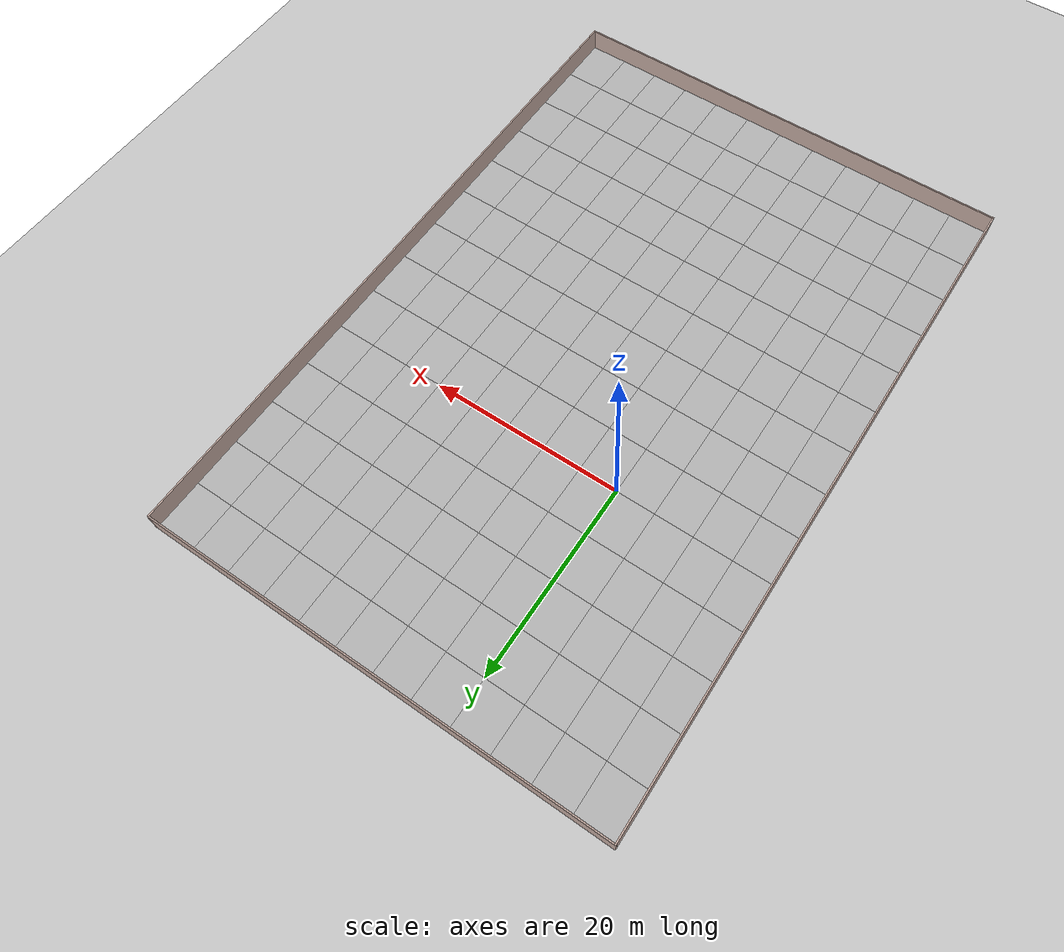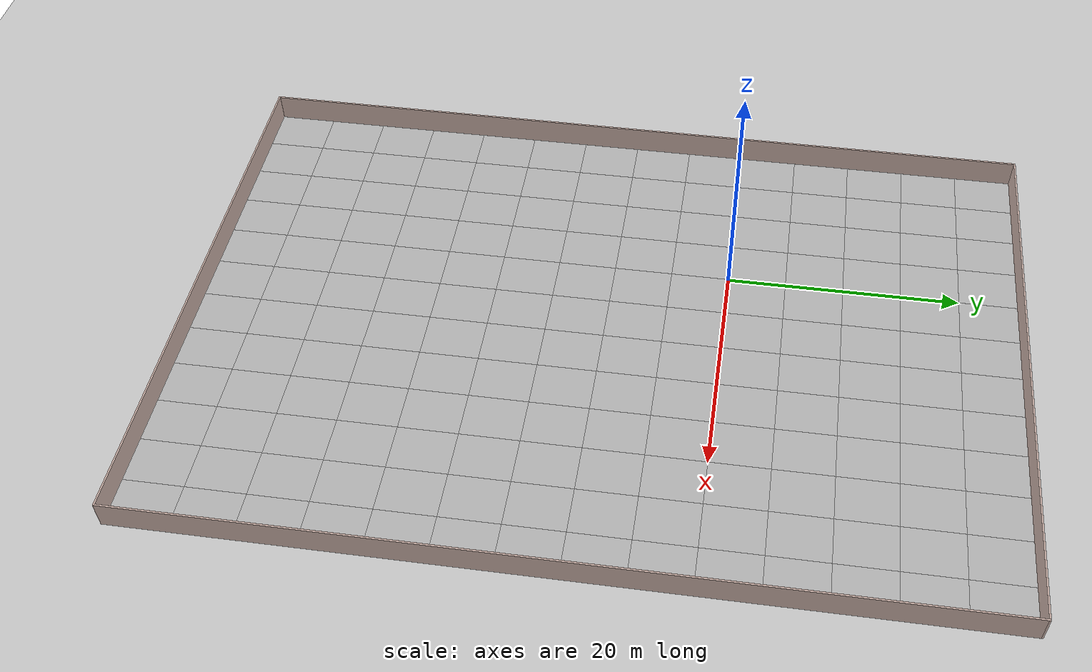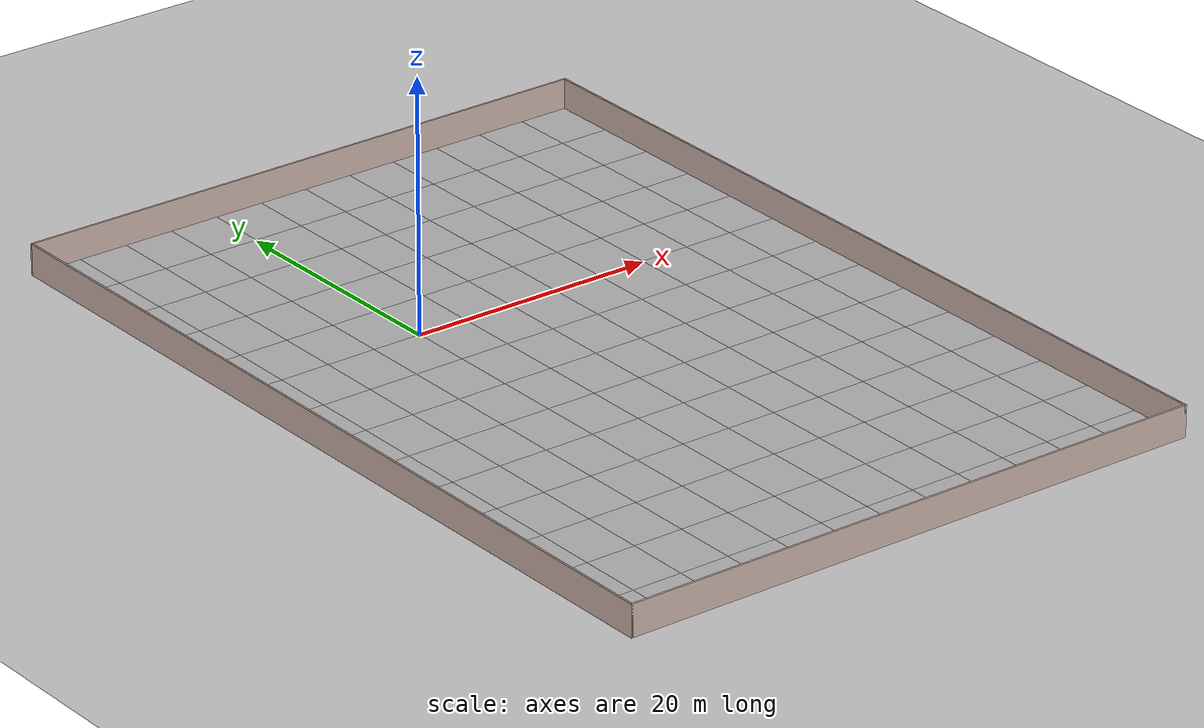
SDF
<sdf version="1.6">
 <world name="default">
  <light name="sun" type="directional">
   <pose>0 0 10 0 -0 0</pose>
   <diffuse>0.8 0.8 0.8 1</diffuse>
   <specular>0.2 0.2 0.2 1</specular>
   <attenuation>
    <range>1000</range>
    <constant>0.9</constant>
    <linear>0.01</linear>
    <quadratic>0.001</quadratic>
   </attenuation>
   <direction>-0.5 0.1 -0.9</direction>
  </light>
  <model name="ground_plane">
   <static>1</static>
   <link name="link">
    <collision name="collision">
     <geometry><plane><normal>0 0 1</normal><size>100 100</size></plane></geometry>
     <surface>
      <contact><collide_bitmask>65535</collide_bitmask></contact>
      <friction><ode><mu>100</mu><mu2>50</mu2></ode></friction>
     </surface>
    </collision>
    <visual name="visual">
     <cast_shadows>0</cast_shadows>
     <geometry><plane><normal>0 0 1</normal><size>100 100</size></plane></geometry>
     <material>
      <script><uri>file://media/materials/scripts/gazebo.material</uri><name>Gazebo/Grey</name></script>
     </material>
    </visual>
   </link>
  </model>
  <gravity>0 0 -9.8</gravity>
  <magnetic_field>6e-06 2.3e-05 -4.2e-05</magnetic_field>
  <atmosphere type="adiabatic"/>
  <physics name="default_physics" default="0" type="ode">
   <max_step_size>0.001</max_step_size>
   <real_time_factor>1</real_time_factor>
   <real_time_update_rate>1000</real_time_update_rate>
  </physics>
  <scene><ambient>0.4 0.4 0.4 1</ambient><background>0.7 0.7 0.7 1</background><shadows>1</shadows></scene>
  <spherical_coordinates>
   <surface_model>EARTH_WGS84</surface_model>
   <latitude_deg>0</latitude_deg>
   <longitude_deg>0</longitude_deg>
   <elevation>0</elevation>
   <heading_deg>0</heading_deg>
  </spherical_coordinates>
  <model name="mud_box">
   <static>1</static>
   <link name="link">
    <collision name="collision"><geometry><box><size>8 10 0.2</size></box></geometry></collision>
    <visual name="visual_1">
     <pose>-2 2.5 0 0 -0 0</pose>
     <cast_shadows>0</cast_shadows>
     <geometry><box><size>4 5 0.2</size></box></geometry>
     <material>
      <script>
       <uri>model://mud_box/materials/scripts</uri>
       <uri>model://mud_box/materials/textures</uri>
       <name>vrc/mud</name>
      </script>
     </material>
    </visual>
    <visual name="visual_2">
     <pose>2 2.5 0 0 -0 0</pose>
     <cast_shadows>0</cast_shadows>
     <geometry><box><size>4 5 0.2</size></box></geometry>
     <material>
      <script>
       <uri>model://mud_box/materials/scripts</uri>
       <uri>model://mud_box/materials/textures</uri>
       <name>vrc/mud</name>
      </script>
     </material>
    </visual>
    <visual name="visual_3">
     <pose>2 -2.5 0 0 -0 0</pose>
     <cast_shadows>0</cast_shadows>
     <geometry><box><size>4 5 0.2</size></box></geometry>
     <material>
      <script>
       <uri>model://mud_box/materials/scripts</uri>
       <uri>model://mud_box/materials/textures</uri>
       <name>vrc/mud</name>
      </script>
     </material>
    </visual>
    <visual name="visual_4">
     <pose>-2 -2.5 0 0 -0 0</pose>
     <cast_shadows>0</cast_shadows>
     <geometry><box><size>4 5 0.2</size></box></geometry>
     <material>
      <script>
       <uri>model://mud_box/materials/scripts</uri>
       <uri>model://mud_box/materials/textures</uri>
       <name>vrc/mud</name>
      </script>
     </material>
    </visual>
   </link>
   <pose>4 0 0 0 -0 0</pose>
  </model>
  <model name="mud_box_clone">
   <static>1</static>
   <link name="link">
    <collision name="collision"><geometry><box><size>8 10 0.2</size></box></geometry></collision>
    <visual name="visual_1">
     <pose>-2 2.5 0 0 -0 0</pose>
     <cast_shadows>0</cast_shadows>
     <geometry><box><size>4 5 0.2</size></box></geometry>
     <material>
      <script>
       <uri>model://mud_box/materials/scripts</uri>
       <uri>model://mud_box/materials/textures</uri>
       <name>vrc/mud</name>
      </script>
     </material>
    </visual>
    <visual name="visual_2">
     <pose>2 2.5 0 0 -0 0</pose>
     <cast_shadows>0</cast_shadows>
     <geometry><box><size>4 5 0.2</size></box></geometry>
     <material>
      <script>
       <uri>model://mud_box/materials/scripts</uri>
       <uri>model://mud_box/materials/textures</uri>
       <name>vrc/mud</name>
      </script>
     </material>
    </visual>
    <visual name="visual_3">
     <pose>2 -2.5 0 0 -0 0</pose>
     <cast_shadows>0</cast_shadows>
     <geometry><box><size>4 5 0.2</size></box></geometry>
     <material>
      <script>
       <uri>model://mud_box/materials/scripts</uri>
       <uri>model://mud_box/materials/textures</uri>
       <name>vrc/mud</name>
      </script>
     </material>
    </visual>
    <visual name="visual_4">
     <pose>-2 -2.5 0 0 -0 0</pose>
     <cast_shadows>0</cast_shadows>
     <geometry><box><size>4 5 0.2</size></box></geometry>
     <material>
      <script>
       <uri>model://mud_box/materials/scripts</uri>
       <uri>model://mud_box/materials/textures</uri>
       <name>vrc/mud</name>
      </script>
     </material>
    </visual>
   </link>
   <pose>-4 0 0 0 -0 0</pose>
  </model>
  <model name="mud_box_clone_clone">
   <static>1</static>
   <link name="link">
    <collision name="collision"><geometry><box><size>8 10 0.2</size></box></geometry></collision>
    <visual name="visual_1">
     <pose>-2 2.5 0 0 -0 0</pose>
     <cast_shadows>0</cast_shadows>
     <geometry><box><size>4 5 0.2</size></box></geometry>
     <material>
      <script>
       <uri>model://mud_box/materials/scripts</uri>
       <uri>model://mud_box/materials/textures</uri>
       <name>vrc/mud</name>
      </script>
     </material>
    </visual>
    <visual name="visual_2">
     <pose>2 2.5 0 0 -0 0</pose>
     <cast_shadows>0</cast_shadows>
     <geometry><box><size>4 5 0.2</size></box></geometry>
     <material>
      <script>
       <uri>model://mud_box/materials/scripts</uri>
       <uri>model://mud_box/materials/textures</uri>
       <name>vrc/mud</name>
      </script>
     </material>
    </visual>
    <visual name="visual_3">
     <pose>2 -2.5 0 0 -0 0</pose>
     <cast_shadows>0</cast_shadows>
     <geometry><box><size>4 5 0.2</size></box></geometry>
     <material>
      <script>
       <uri>model://mud_box/materials/scripts</uri>
       <uri>model://mud_box/materials/textures</uri>
       <name>vrc/mud</name>
      </script>
     </material>
    </visual>
    <visual name="visual_4">
     <pose>-2 -2.5 0 0 -0 0</pose>
     <cast_shadows>0</cast_shadows>
     <geometry><box><size>4 5 0.2</size></box></geometry>
     <material>
      <script>
       <uri>model://mud_box/materials/scripts</uri>
       <uri>model://mud_box/materials/textures</uri>
       <name>vrc/mud</name>
      </script>
     </material>
    </visual>
   </link>
   <pose>-4 -10 0 0 -0 0</pose>
  </model>
  <model name="mud_box_clone_clone_0">
   <static>1</static>
   <link name="link">
    <collision name="collision"><geometry><box><size>8 10 0.2</size></box></geometry></collision>
    <visual name="visual_1">
     <pose>-2 2.5 0 0 -0 0</pose>
     <cast_shadows>0</cast_shadows>
     <geometry><box><size>4 5 0.2</size></box></geometry>
     <material>
      <script>
       <uri>model://mud_box/materials/scripts</uri>
       <uri>model://mud_box/materials/textures</uri>
       <name>vrc/mud</name>
      </script>
     </material>
    </visual>
    <visual name="visual_2">
     <pose>2 2.5 0 0 -0 0</pose>
     <cast_shadows>0</cast_shadows>
     <geometry><box><size>4 5 0.2</size></box></geometry>
     <material>
      <script>
       <uri>model://mud_box/materials/scripts</uri>
       <uri>model://mud_box/materials/textures</uri>
       <name>vrc/mud</name>
      </script>
     </material>
    </visual>
    <visual name="visual_3">
     <pose>2 -2.5 0 0 -0 0</pose>
     <cast_shadows>0</cast_shadows>
     <geometry><box><size>4 5 0.2</size></box></geometry>
     <material>
      <script>
       <uri>model://mud_box/materials/scripts</uri>
       <uri>model://mud_box/materials/textures</uri>
       <name>vrc/mud</name>
      </script>
     </material>
    </visual>
    <visual name="visual_4">
     <pose>-2 -2.5 0 0 -0 0</pose>
     <cast_shadows>0</cast_shadows>
     <geometry><box><size>4 5 0.2</size></box></geometry>
     <material>
      <script>
       <uri>model://mud_box/materials/scripts</uri>
       <uri>model://mud_box/materials/textures</uri>
       <name>vrc/mud</name>
      </script>
     </material>
    </visual>
   </link>
   <pose>4 -10 0 0 -0 0</pose>
  </model>
  <model name="mud_box_clone_clone_1">
   <static>1</static>
   <link name="link">
    <collision name="collision"><geometry><box><size>8 10 0.2</size></box></geometry></collision>
    <visual name="visual_1">
     <pose>-2 2.5 0 0 -0 0</pose>
     <cast_shadows>0</cast_shadows>
     <geometry><box><size>4 5 0.2</size></box></geometry>
     <material>
      <script>
       <uri>model://mud_box/materials/scripts</uri>
       <uri>model://mud_box/materials/textures</uri>
       <name>vrc/mud</name>
      </script>
     </material>
    </visual>
    <visual name="visual_2">
     <pose>2 2.5 0 0 -0 0</pose>
     <cast_shadows>0</cast_shadows>
     <geometry><box><size>4 5 0.2</size></box></geometry>
     <material>
      <script>
       <uri>model://mud_box/materials/scripts</uri>
       <uri>model://mud_box/materials/textures</uri>
       <name>vrc/mud</name>
      </script>
     </material>
    </visual>
    <visual name="visual_3">
     <pose>2 -2.5 0 0 -0 0</pose>
     <cast_shadows>0</cast_shadows>
     <geometry><box><size>4 5 0.2</size></box></geometry>
     <material>
      <script>
       <uri>model://mud_box/materials/scripts</uri>
       <uri>model://mud_box/materials/textures</uri>
       <name>vrc/mud</name>
      </script>
     </material>
    </visual>
    <visual name="visual_4">
     <pose>-2 -2.5 0 0 -0 0</pose>
     <cast_shadows>0</cast_shadows>
     <geometry><box><size>4 5 0.2</size></box></geometry>
     <material>
      <script>
       <uri>model://mud_box/materials/scripts</uri>
       <uri>model://mud_box/materials/textures</uri>
       <name>vrc/mud</name>
      </script>
     </material>
    </visual>
   </link>
   <pose>12 0 0 0 -0 0</pose>
  </model>
  <model name="mud_box_clone_clone_2">
   <static>1</static>
   <link name="link">
    <collision name="collision"><geometry><box><size>8 10 0.2</size></box></geometry></collision>
    <visual name="visual_1">
     <pose>-2 2.5 0 0 -0 0</pose>
     <cast_shadows>0</cast_shadows>
     <geometry><box><size>4 5 0.2</size></box></geometry>
     <material>
      <script>
       <uri>model://mud_box/materials/scripts</uri>
       <uri>model://mud_box/materials/textures</uri>
       <name>vrc/mud</name>
      </script>
     </material>
    </visual>
    <visual name="visual_2">
     <pose>2 2.5 0 0 -0 0</pose>
     <cast_shadows>0</cast_shadows>
     <geometry><box><size>4 5 0.2</size></box></geometry>
     <material>
      <script>
       <uri>model://mud_box/materials/scripts</uri>
       <uri>model://mud_box/materials/textures</uri>
       <name>vrc/mud</name>
      </script>
     </material>
    </visual>
    <visual name="visual_3">
     <pose>2 -2.5 0 0 -0 0</pose>
     <cast_shadows>0</cast_shadows>
     <geometry><box><size>4 5 0.2</size></box></geometry>
     <material>
      <script>
       <uri>model://mud_box/materials/scripts</uri>
       <uri>model://mud_box/materials/textures</uri>
       <name>vrc/mud</name>
      </script>
     </material>
    </visual>
    <visual name="visual_4">
     <pose>-2 -2.5 0 0 -0 0</pose>
     <cast_shadows>0</cast_shadows>
     <geometry><box><size>4 5 0.2</size></box></geometry>
     <material>
      <script>
       <uri>model://mud_box/materials/scripts</uri>
       <uri>model://mud_box/materials/textures</uri>
       <name>vrc/mud</name>
      </script>
     </material>
    </visual>
   </link>
   <pose>-12 0 0 0 -0 0</pose>
  </model>
  <model name="mud_box_clone_clone_3">
   <static>1</static>
   <link name="link">
    <collision name="collision"><geometry><box><size>8 10 0.2</size></box></geometry></collision>
    <visual name="visual_1">
     <pose>-2 2.5 0 0 -0 0</pose>
     <cast_shadows>0</cast_shadows>
     <geometry><box><size>4 5 0.2</size></box></geometry>
     <material>
      <script>
       <uri>model://mud_box/materials/scripts</uri>
       <uri>model://mud_box/materials/textures</uri>
       <name>vrc/mud</name>
      </script>
     </material>
    </visual>
    <visual name="visual_2">
     <pose>2 2.5 0 0 -0 0</pose>
     <cast_shadows>0</cast_shadows>
     <geometry><box><size>4 5 0.2</size></box></geometry>
     <material>
      <script>
       <uri>model://mud_box/materials/scripts</uri>
       <uri>model://mud_box/materials/textures</uri>
       <name>vrc/mud</name>
      </script>
     </material>
    </visual>
    <visual name="visual_3">
     <pose>2 -2.5 0 0 -0 0</pose>
     <cast_shadows>0</cast_shadows>
     <geometry><box><size>4 5 0.2</size></box></geometry>
     <material>
      <script>
       <uri>model://mud_box/materials/scripts</uri>
       <uri>model://mud_box/materials/textures</uri>
       <name>vrc/mud</name>
      </script>
     </material>
    </visual>
    <visual name="visual_4">
     <pose>-2 -2.5 0 0 -0 0</pose>
     <cast_shadows>0</cast_shadows>
     <geometry><box><size>4 5 0.2</size></box></geometry>
     <material>
      <script>
       <uri>model://mud_box/materials/scripts</uri>
       <uri>model://mud_box/materials/textures</uri>
       <name>vrc/mud</name>
      </script>
     </material>
    </visual>
   </link>
   <pose>-12 -10 0 0 -0 0</pose>
  </model>
  <model name="mud_box_clone_clone_4">
   <static>1</static>
   <link name="link">
    <collision name="collision"><geometry><box><size>8 10 0.2</size></box></geometry></collision>
    <visual name="visual_1">
     <pose>-2 2.5 0 0 -0 0</pose>
     <cast_shadows>0</cast_shadows>
     <geometry><box><size>4 5 0.2</size></box></geometry>
     <material>
      <script>
       <uri>model://mud_box/materials/scripts</uri>
       <uri>model://mud_box/materials/textures</uri>
       <name>vrc/mud</name>
      </script>
     </material>
    </visual>
    <visual name="visual_2">
     <pose>2 2.5 0 0 -0 0</pose>
     <cast_shadows>0</cast_shadows>
     <geometry><box><size>4 5 0.2</size></box></geometry>
     <material>
      <script>
       <uri>model://mud_box/materials/scripts</uri>
       <uri>model://mud_box/materials/textures</uri>
       <name>vrc/mud</name>
      </script>
     </material>
    </visual>
    <visual name="visual_3">
     <pose>2 -2.5 0 0 -0 0</pose>
     <cast_shadows>0</cast_shadows>
     <geometry><box><size>4 5 0.2</size></box></geometry>
     <material>
      <script>
       <uri>model://mud_box/materials/scripts</uri>
       <uri>model://mud_box/materials/textures</uri>
       <name>vrc/mud</name>
      </script>
     </material>
    </visual>
    <visual name="visual_4">
     <pose>-2 -2.5 0 0 -0 0</pose>
     <cast_shadows>0</cast_shadows>
     <geometry><box><size>4 5 0.2</size></box></geometry>
     <material>
      <script>
       <uri>model://mud_box/materials/scripts</uri>
       <uri>model://mud_box/materials/textures</uri>
       <name>vrc/mud</name>
      </script>
     </material>
    </visual>
   </link>
   <pose>12 -10 0 0 -0 0</pose>
  </model>
  <model name="mud_box_clone_clone_5">
   <static>1</static>
   <link name="link">
    <collision name="collision"><geometry><box><size>8 10 0.2</size></box></geometry></collision>
    <visual name="visual_1">
     <pose>-2 2.5 0 0 -0 0</pose>
     <cast_shadows>0</cast_shadows>
     <geometry><box><size>4 5 0.2</size></box></geometry>
     <material>
      <script>
       <uri>model://mud_box/materials/scripts</uri>
       <uri>model://mud_box/materials/textures</uri>
       <name>vrc/mud</name>
      </script>
     </material>
    </visual>
    <visual name="visual_2">
     <pose>2 2.5 0 0 -0 0</pose>
     <cast_shadows>0</cast_shadows>
     <geometry><box><size>4 5 0.2</size></box></geometry>
     <material>
      <script>
       <uri>model://mud_box/materials/scripts</uri>
       <uri>model://mud_box/materials/textures</uri>
       <name>vrc/mud</name>
      </script>
     </material>
    </visual>
    <visual name="visual_3">
     <pose>2 -2.5 0 0 -0 0</pose>
     <cast_shadows>0</cast_shadows>
     <geometry><box><size>4 5 0.2</size></box></geometry>
     <material>
      <script>
       <uri>model://mud_box/materials/scripts</uri>
       <uri>model://mud_box/materials/textures</uri>
       <name>vrc/mud</name>
      </script>
     </material>
    </visual>
    <visual name="visual_4">
     <pose>-2 -2.5 0 0 -0 0</pose>
     <cast_shadows>0</cast_shadows>
     <geometry><box><size>4 5 0.2</size></box></geometry>
     <material>
      <script>
       <uri>model://mud_box/materials/scripts</uri>
       <uri>model://mud_box/materials/textures</uri>
       <name>vrc/mud</name>
      </script>
     </material>
    </visual>
   </link>
   <pose>-12 10 0 0 -0 0</pose>
  </model>
  <model name="mud_box_clone_clone_6">
   <static>1</static>
   <link name="link">
    <collision name="collision"><geometry><box><size>8 10 0.2</size></box></geometry></collision>
    <visual name="visual_1">
     <pose>-2 2.5 0 0 -0 0</pose>
     <cast_shadows>0</cast_shadows>
     <geometry><box><size>4 5 0.2</size></box></geometry>
     <material>
      <script>
       <uri>model://mud_box/materials/scripts</uri>
       <uri>model://mud_box/materials/textures</uri>
       <name>vrc/mud</name>
      </script>
     </material>
    </visual>
    <visual name="visual_2">
     <pose>2 2.5 0 0 -0 0</pose>
     <cast_shadows>0</cast_shadows>
     <geometry><box><size>4 5 0.2</size></box></geometry>
     <material>
      <script>
       <uri>model://mud_box/materials/scripts</uri>
       <uri>model://mud_box/materials/textures</uri>
       <name>vrc/mud</name>
      </script>
     </material>
    </visual>
    <visual name="visual_3">
     <pose>2 -2.5 0 0 -0 0</pose>
     <cast_shadows>0</cast_shadows>
     <geometry><box><size>4 5 0.2</size></box></geometry>
     <material>
      <script>
       <uri>model://mud_box/materials/scripts</uri>
       <uri>model://mud_box/materials/textures</uri>
       <name>vrc/mud</name>
      </script>
     </material>
    </visual>
    <visual name="visual_4">
     <pose>-2 -2.5 0 0 -0 0</pose>
     <cast_shadows>0</cast_shadows>
     <geometry><box><size>4 5 0.2</size></box></geometry>
     <material>
      <script>
       <uri>model://mud_box/materials/scripts</uri>
       <uri>model://mud_box/materials/textures</uri>
       <name>vrc/mud</name>
      </script>
     </material>
    </visual>
   </link>
   <pose>-4 10 0 0 -0 0</pose>
  </model>
  <model name="mud_box_clone_clone_7">
   <static>1</static>
   <link name="link">
    <collision name="collision"><geometry><box><size>8 10 0.2</size></box></geometry></collision>
    <visual name="visual_1">
     <pose>-2 2.5 0 0 -0 0</pose>
     <cast_shadows>0</cast_shadows>
     <geometry><box><size>4 5 0.2</size></box></geometry>
     <material>
      <script>
       <uri>model://mud_box/materials/scripts</uri>
       <uri>model://mud_box/materials/textures</uri>
       <name>vrc/mud</name>
      </script>
     </material>
    </visual>
    <visual name="visual_2">
     <pose>2 2.5 0 0 -0 0</pose>
     <cast_shadows>0</cast_shadows>
     <geometry><box><size>4 5 0.2</size></box></geometry>
     <material>
      <script>
       <uri>model://mud_box/materials/scripts</uri>
       <uri>model://mud_box/materials/textures</uri>
       <name>vrc/mud</name>
      </script>
     </material>
    </visual>
    <visual name="visual_3">
     <pose>2 -2.5 0 0 -0 0</pose>
     <cast_shadows>0</cast_shadows>
     <geometry><box><size>4 5 0.2</size></box></geometry>
     <material>
      <script>
       <uri>model://mud_box/materials/scripts</uri>
       <uri>model://mud_box/materials/textures</uri>
       <name>vrc/mud</name>
      </script>
     </material>
    </visual>
    <visual name="visual_4">
     <pose>-2 -2.5 0 0 -0 0</pose>
     <cast_shadows>0</cast_shadows>
     <geometry><box><size>4 5 0.2</size></box></geometry>
     <material>
      <script>
       <uri>model://mud_box/materials/scripts</uri>
       <uri>model://mud_box/materials/textures</uri>
       <name>vrc/mud</name>
      </script>
     </material>
    </visual>
   </link>
   <pose>4 10 0 0 -0 0</pose>
  </model>
  <model name="mud_box_clone_clone_8">
   <static>1</static>
   <link name="link">
    <collision name="collision"><geometry><box><size>8 10 0.2</size></box></geometry></collision>
    <visual name="visual_1">
     <pose>-2 2.5 0 0 -0 0</pose>
     <cast_shadows>0</cast_shadows>
     <geometry><box><size>4 5 0.2</size></box></geometry>
     <material>
      <script>
       <uri>model://mud_box/materials/scripts</uri>
       <uri>model://mud_box/materials/textures</uri>
       <name>vrc/mud</name>
      </script>
     </material>
    </visual>
    <visual name="visual_2">
     <pose>2 2.5 0 0 -0 0</pose>
     <cast_shadows>0</cast_shadows>
     <geometry><box><size>4 5 0.2</size></box></geometry>
     <material>
      <script>
       <uri>model://mud_box/materials/scripts</uri>
       <uri>model://mud_box/materials/textures</uri>
       <name>vrc/mud</name>
      </script>
     </material>
    </visual>
    <visual name="visual_3">
     <pose>2 -2.5 0 0 -0 0</pose>
     <cast_shadows>0</cast_shadows>
     <geometry><box><size>4 5 0.2</size></box></geometry>
     <material>
      <script>
       <uri>model://mud_box/materials/scripts</uri>
       <uri>model://mud_box/materials/textures</uri>
       <name>vrc/mud</name>
      </script>
     </material>
    </visual>
    <visual name="visual_4">
     <pose>-2 -2.5 0 0 -0 0</pose>
     <cast_shadows>0</cast_shadows>
     <geometry><box><size>4 5 0.2</size></box></geometry>
     <material>
      <script>
       <uri>model://mud_box/materials/scripts</uri>
       <uri>model://mud_box/materials/textures</uri>
       <name>vrc/mud</name>
      </script>
     </material>
    </visual>
   </link>
   <pose>12 10 0 0 -0 0</pose>
  </model>
  <model name="mud_box_clone_clone_4_clone">
   <static>1</static>
   <link name="link">
    <collision name="collision"><geometry><box><size>8 10 0.2</size></box></geometry></collision>
    <visual name="visual_1">
     <pose>-2 2.5 0 0 -0 0</pose>
     <cast_shadows>0</cast_shadows>
     <geometry><box><size>4 5 0.2</size></box></geometry>
     <material>
      <script>
       <uri>model://mud_box/materials/scripts</uri>
       <uri>model://mud_box/materials/textures</uri>
       <name>vrc/mud</name>
      </script>
     </material>
    </visual>
    <visual name="visual_2">
     <pose>2 2.5 0 0 -0 0</pose>
     <cast_shadows>0</cast_shadows>
     <geometry><box><size>4 5 0.2</size></box></geometry>
     <material>
      <script>
       <uri>model://mud_box/materials/scripts</uri>
       <uri>model://mud_box/materials/textures</uri>
       <name>vrc/mud</name>
      </script>
     </material>
    </visual>
    <visual name="visual_3">
     <pose>2 -2.5 0 0 -0 0</pose>
     <cast_shadows>0</cast_shadows>
     <geometry><box><size>4 5 0.2</size></box></geometry>
     <material>
      <script>
       <uri>model://mud_box/materials/scripts</uri>
       <uri>model://mud_box/materials/textures</uri>
       <name>vrc/mud</name>
      </script>
     </material>
    </visual>
    <visual name="visual_4">
     <pose>-2 -2.5 0 0 -0 0</pose>
     <cast_shadows>0</cast_shadows>
     <geometry><box><size>4 5 0.2</size></box></geometry>
     <material>
      <script>
       <uri>model://mud_box/materials/scripts</uri>
       <uri>model://mud_box/materials/textures</uri>
       <name>vrc/mud</name>
      </script>
     </material>
    </visual>
   </link>
   <pose>12 -20 0 0 -0 0</pose>
  </model>
  <model name="mud_box_clone_clone_4_clone_0">
   <static>1</static>
   <link name="link">
    <collision name="collision"><geometry><box><size>8 10 0.2</size></box></geometry></collision>
    <visual name="visual_1">
     <pose>-2 2.5 0 0 -0 0</pose>
     <cast_shadows>0</cast_shadows>
     <geometry><box><size>4 5 0.2</size></box></geometry>
     <material>
      <script>
       <uri>model://mud_box/materials/scripts</uri>
       <uri>model://mud_box/materials/textures</uri>
       <name>vrc/mud</name>
      </script>
     </material>
    </visual>
    <visual name="visual_2">
     <pose>2 2.5 0 0 -0 0</pose>
     <cast_shadows>0</cast_shadows>
     <geometry><box><size>4 5 0.2</size></box></geometry>
     <material>
      <script>
       <uri>model://mud_box/materials/scripts</uri>
       <uri>model://mud_box/materials/textures</uri>
       <name>vrc/mud</name>
      </script>
     </material>
    </visual>
    <visual name="visual_3">
     <pose>2 -2.5 0 0 -0 0</pose>
     <cast_shadows>0</cast_shadows>
     <geometry><box><size>4 5 0.2</size></box></geometry>
     <material>
      <script>
       <uri>model://mud_box/materials/scripts</uri>
       <uri>model://mud_box/materials/textures</uri>
       <name>vrc/mud</name>
      </script>
     </material>
    </visual>
    <visual name="visual_4">
     <pose>-2 -2.5 0 0 -0 0</pose>
     <cast_shadows>0</cast_shadows>
     <geometry><box><size>4 5 0.2</size></box></geometry>
     <material>
      <script>
       <uri>model://mud_box/materials/scripts</uri>
       <uri>model://mud_box/materials/textures</uri>
       <name>vrc/mud</name>
      </script>
     </material>
    </visual>
   </link>
   <pose>4 -20 0 0 -0 0</pose>
  </model>
  <model name="mud_box_clone_clone_4_clone_1">
   <static>1</static>
   <link name="link">
    <collision name="collision"><geometry><box><size>8 10 0.2</size></box></geometry></collision>
    <visual name="visual_1">
     <pose>-2 2.5 0 0 -0 0</pose>
     <cast_shadows>0</cast_shadows>
     <geometry><box><size>4 5 0.2</size></box></geometry>
     <material>
      <script>
       <uri>model://mud_box/materials/scripts</uri>
       <uri>model://mud_box/materials/textures</uri>
       <name>vrc/mud</name>
      </script>
     </material>
    </visual>
    <visual name="visual_2">
     <pose>2 2.5 0 0 -0 0</pose>
     <cast_shadows>0</cast_shadows>
     <geometry><box><size>4 5 0.2</size></box></geometry>
     <material>
      <script>
       <uri>model://mud_box/materials/scripts</uri>
       <uri>model://mud_box/materials/textures</uri>
       <name>vrc/mud</name>
      </script>
     </material>
    </visual>
    <visual name="visual_3">
     <pose>2 -2.5 0 0 -0 0</pose>
     <cast_shadows>0</cast_shadows>
     <geometry><box><size>4 5 0.2</size></box></geometry>
     <material>
      <script>
       <uri>model://mud_box/materials/scripts</uri>
       <uri>model://mud_box/materials/textures</uri>
       <name>vrc/mud</name>
      </script>
     </material>
    </visual>
    <visual name="visual_4">
     <pose>-2 -2.5 0 0 -0 0</pose>
     <cast_shadows>0</cast_shadows>
     <geometry><box><size>4 5 0.2</size></box></geometry>
     <material>
      <script>
       <uri>model://mud_box/materials/scripts</uri>
       <uri>model://mud_box/materials/textures</uri>
       <name>vrc/mud</name>
      </script>
     </material>
    </visual>
   </link>
   <pose>-4 -20 0 0 -0 0</pose>
  </model>
  <model name="mud_box_clone_clone_4_clone_2">
   <static>1</static>
   <link name="link">
    <collision name="collision"><geometry><box><size>8 10 0.2</size></box></geometry></collision>
    <visual name="visual_1">
     <pose>-2 2.5 0 0 -0 0</pose>
     <cast_shadows>0</cast_shadows>
     <geometry><box><size>4 5 0.2</size></box></geometry>
     <material>
      <script>
       <uri>model://mud_box/materials/scripts</uri>
       <uri>model://mud_box/materials/textures</uri>
       <name>vrc/mud</name>
      </script>
     </material>
    </visual>
    <visual name="visual_2">
     <pose>2 2.5 0 0 -0 0</pose>
     <cast_shadows>0</cast_shadows>
     <geometry><box><size>4 5 0.2</size></box></geometry>
     <material>
      <script>
       <uri>model://mud_box/materials/scripts</uri>
       <uri>model://mud_box/materials/textures</uri>
       <name>vrc/mud</name>
      </script>
     </material>
    </visual>
    <visual name="visual_3">
     <pose>2 -2.5 0 0 -0 0</pose>
     <cast_shadows>0</cast_shadows>
     <geometry><box><size>4 5 0.2</size></box></geometry>
     <material>
      <script>
       <uri>model://mud_box/materials/scripts</uri>
       <uri>model://mud_box/materials/textures</uri>
       <name>vrc/mud</name>
      </script>
     </material>
    </visual>
    <visual name="visual_4">
     <pose>-2 -2.5 0 0 -0 0</pose>
     <cast_shadows>0</cast_shadows>
     <geometry><box><size>4 5 0.2</size></box></geometry>
     <material>
      <script>
       <uri>model://mud_box/materials/scripts</uri>
       <uri>model://mud_box/materials/textures</uri>
       <name>vrc/mud</name>
      </script>
     </material>
    </visual>
   </link>
   <pose>-12 -20 0 0 -0 0</pose>
  </model>
  <model name="mud_box_clone_clone_4_clone_clone">
   <static>1</static>
   <link name="link">
    <collision name="collision"><geometry><box><size>8 10 0.2</size></box></geometry></collision>
    <visual name="visual_1">
     <pose>-2 2.5 0 0 -0 0</pose>
     <cast_shadows>0</cast_shadows>
     <geometry><box><size>4 5 0.2</size></box></geometry>
     <material>
      <script>
       <uri>model://mud_box/materials/scripts</uri>
       <uri>model://mud_box/materials/textures</uri>
       <name>vrc/mud</name>
      </script>
     </material>
    </visual>
    <visual name="visual_2">
     <pose>2 2.5 0 0 -0 0</pose>
     <cast_shadows>0</cast_shadows>
     <geometry><box><size>4 5 0.2</size></box></geometry>
     <material>
      <script>
       <uri>model://mud_box/materials/scripts</uri>
       <uri>model://mud_box/materials/textures</uri>
       <name>vrc/mud</name>
      </script>
     </material>
    </visual>
    <visual name="visual_3">
     <pose>2 -2.5 0 0 -0 0</pose>
     <cast_shadows>0</cast_shadows>
     <geometry><box><size>4 5 0.2</size></box></geometry>
     <material>
      <script>
       <uri>model://mud_box/materials/scripts</uri>
       <uri>model://mud_box/materials/textures</uri>
       <name>vrc/mud</name>
      </script>
     </material>
    </visual>
    <visual name="visual_4">
     <pose>-2 -2.5 0 0 -0 0</pose>
     <cast_shadows>0</cast_shadows>
     <geometry><box><size>4 5 0.2</size></box></geometry>
     <material>
      <script>
       <uri>model://mud_box/materials/scripts</uri>
       <uri>model://mud_box/materials/textures</uri>
       <name>vrc/mud</name>
      </script>
     </material>
    </visual>
   </link>
   <pose>20 -20 0 0 -0 0</pose>
  </model>
  <model name="mud_box_clone_clone_4_clone_clone_0">
   <static>1</static>
   <link name="link">
    <collision name="collision"><geometry><box><size>8 10 0.2</size></box></geometry></collision>
    <visual name="visual_1">
     <pose>-2 2.5 0 0 -0 0</pose>
     <cast_shadows>0</cast_shadows>
     <geometry><box><size>4 5 0.2</size></box></geometry>
     <material>
      <script>
       <uri>model://mud_box/materials/scripts</uri>
       <uri>model://mud_box/materials/textures</uri>
       <name>vrc/mud</name>
      </script>
     </material>
    </visual>
    <visual name="visual_2">
     <pose>2 2.5 0 0 -0 0</pose>
     <cast_shadows>0</cast_shadows>
     <geometry><box><size>4 5 0.2</size></box></geometry>
     <material>
      <script>
       <uri>model://mud_box/materials/scripts</uri>
       <uri>model://mud_box/materials/textures</uri>
       <name>vrc/mud</name>
      </script>
     </material>
    </visual>
    <visual name="visual_3">
     <pose>2 -2.5 0 0 -0 0</pose>
     <cast_shadows>0</cast_shadows>
     <geometry><box><size>4 5 0.2</size></box></geometry>
     <material>
      <script>
       <uri>model://mud_box/materials/scripts</uri>
       <uri>model://mud_box/materials/textures</uri>
       <name>vrc/mud</name>
      </script>
     </material>
    </visual>
    <visual name="visual_4">
     <pose>-2 -2.5 0 0 -0 0</pose>
     <cast_shadows>0</cast_shadows>
     <geometry><box><size>4 5 0.2</size></box></geometry>
     <material>
      <script>
       <uri>model://mud_box/materials/scripts</uri>
       <uri>model://mud_box/materials/textures</uri>
       <name>vrc/mud</name>
      </script>
     </material>
    </visual>
   </link>
   <pose>20 -10 0 0 -0 0</pose>
  </model>
  <model name="mud_box_clone_clone_4_clone_clone_1">
   <static>1</static>
   <link name="link">
    <collision name="collision"><geometry><box><size>8 10 0.2</size></box></geometry></collision>
    <visual name="visual_1">
     <pose>-2 2.5 0 0 -0 0</pose>
     <cast_shadows>0</cast_shadows>
     <geometry><box><size>4 5 0.2</size></box></geometry>
     <material>
      <script>
       <uri>model://mud_box/materials/scripts</uri>
       <uri>model://mud_box/materials/textures</uri>
       <name>vrc/mud</name>
      </script>
     </material>
    </visual>
    <visual name="visual_2">
     <pose>2 2.5 0 0 -0 0</pose>
     <cast_shadows>0</cast_shadows>
     <geometry><box><size>4 5 0.2</size></box></geometry>
     <material>
      <script>
       <uri>model://mud_box/materials/scripts</uri>
       <uri>model://mud_box/materials/textures</uri>
       <name>vrc/mud</name>
      </script>
     </material>
    </visual>
    <visual name="visual_3">
     <pose>2 -2.5 0 0 -0 0</pose>
     <cast_shadows>0</cast_shadows>
     <geometry><box><size>4 5 0.2</size></box></geometry>
     <material>
      <script>
       <uri>model://mud_box/materials/scripts</uri>
       <uri>model://mud_box/materials/textures</uri>
       <name>vrc/mud</name>
      </script>
     </material>
    </visual>
    <visual name="visual_4">
     <pose>-2 -2.5 0 0 -0 0</pose>
     <cast_shadows>0</cast_shadows>
     <geometry><box><size>4 5 0.2</size></box></geometry>
     <material>
      <script>
       <uri>model://mud_box/materials/scripts</uri>
       <uri>model://mud_box/materials/textures</uri>
       <name>vrc/mud</name>
      </script>
     </material>
    </visual>
   </link>
   <pose>20 0 0 0 -0 0</pose>
  </model>
  <model name="mud_box_clone_clone_4_clone_clone_2">
   <static>1</static>
   <link name="link">
    <collision name="collision"><geometry><box><size>8 10 0.2</size></box></geometry></collision>
    <visual name="visual_1">
     <pose>-2 2.5 0 0 -0 0</pose>
     <cast_shadows>0</cast_shadows>
     <geometry><box><size>4 5 0.2</size></box></geometry>
     <material>
      <script>
       <uri>model://mud_box/materials/scripts</uri>
       <uri>model://mud_box/materials/textures</uri>
       <name>vrc/mud</name>
      </script>
     </material>
    </visual>
    <visual name="visual_2">
     <pose>2 2.5 0 0 -0 0</pose>
     <cast_shadows>0</cast_shadows>
     <geometry><box><size>4 5 0.2</size></box></geometry>
     <material>
      <script>
       <uri>model://mud_box/materials/scripts</uri>
       <uri>model://mud_box/materials/textures</uri>
       <name>vrc/mud</name>
      </script>
     </material>
    </visual>
    <visual name="visual_3">
     <pose>2 -2.5 0 0 -0 0</pose>
     <cast_shadows>0</cast_shadows>
     <geometry><box><size>4 5 0.2</size></box></geometry>
     <material>
      <script>
       <uri>model://mud_box/materials/scripts</uri>
       <uri>model://mud_box/materials/textures</uri>
       <name>vrc/mud</name>
      </script>
     </material>
    </visual>
    <visual name="visual_4">
     <pose>-2 -2.5 0 0 -0 0</pose>
     <cast_shadows>0</cast_shadows>
     <geometry><box><size>4 5 0.2</size></box></geometry>
     <material>
      <script>
       <uri>model://mud_box/materials/scripts</uri>
       <uri>model://mud_box/materials/textures</uri>
       <name>vrc/mud</name>
      </script>
     </material>
    </visual>
   </link>
   <pose>20 10 0 0 -0 0</pose>
  </model>
  <model name="mud_box_clone_clone_4_clone_clone_3">
   <static>1</static>
   <link name="link">
    <collision name="collision"><geometry><box><size>8 10 0.2</size></box></geometry></collision>
    <visual name="visual_1">
     <pose>-2 2.5 0 0 -0 0</pose>
     <cast_shadows>0</cast_shadows>
     <geometry><box><size>4 5 0.2</size></box></geometry>
     <material>
      <script>
       <uri>model://mud_box/materials/scripts</uri>
       <uri>model://mud_box/materials/textures</uri>
       <name>vrc/mud</name>
      </script>
     </material>
    </visual>
    <visual name="visual_2">
     <pose>2 2.5 0 0 -0 0</pose>
     <cast_shadows>0</cast_shadows>
     <geometry><box><size>4 5 0.2</size></box></geometry>
     <material>
      <script>
       <uri>model://mud_box/materials/scripts</uri>
       <uri>model://mud_box/materials/textures</uri>
       <name>vrc/mud</name>
      </script>
     </material>
    </visual>
    <visual name="visual_3">
     <pose>2 -2.5 0 0 -0 0</pose>
     <cast_shadows>0</cast_shadows>
     <geometry><box><size>4 5 0.2</size></box></geometry>
     <material>
      <script>
       <uri>model://mud_box/materials/scripts</uri>
       <uri>model://mud_box/materials/textures</uri>
       <name>vrc/mud</name>
      </script>
     </material>
    </visual>
    <visual name="visual_4">
     <pose>-2 -2.5 0 0 -0 0</pose>
     <cast_shadows>0</cast_shadows>
     <geometry><box><size>4 5 0.2</size></box></geometry>
     <material>
      <script>
       <uri>model://mud_box/materials/scripts</uri>
       <uri>model://mud_box/materials/textures</uri>
       <name>vrc/mud</name>
      </script>
     </material>
    </visual>
   </link>
   <pose>20 -30 0 0 -0 0</pose>
  </model>
  <model name="mud_box_clone_clone_4_clone_clone_4">
   <static>1</static>
   <link name="link">
    <collision name="collision"><geometry><box><size>8 10 0.2</size></box></geometry></collision>
    <visual name="visual_1">
     <pose>-2 2.5 0 0 -0 0</pose>
     <cast_shadows>0</cast_shadows>
     <geometry><box><size>4 5 0.2</size></box></geometry>
     <material>
      <script>
       <uri>model://mud_box/materials/scripts</uri>
       <uri>model://mud_box/materials/textures</uri>
       <name>vrc/mud</name>
      </script>
     </material>
    </visual>
    <visual name="visual_2">
     <pose>2 2.5 0 0 -0 0</pose>
     <cast_shadows>0</cast_shadows>
     <geometry><box><size>4 5 0.2</size></box></geometry>
     <material>
      <script>
       <uri>model://mud_box/materials/scripts</uri>
       <uri>model://mud_box/materials/textures</uri>
       <name>vrc/mud</name>
      </script>
     </material>
    </visual>
    <visual name="visual_3">
     <pose>2 -2.5 0 0 -0 0</pose>
     <cast_shadows>0</cast_shadows>
     <geometry><box><size>4 5 0.2</size></box></geometry>
     <material>
      <script>
       <uri>model://mud_box/materials/scripts</uri>
       <uri>model://mud_box/materials/textures</uri>
       <name>vrc/mud</name>
      </script>
     </material>
    </visual>
    <visual name="visual_4">
     <pose>-2 -2.5 0 0 -0 0</pose>
     <cast_shadows>0</cast_shadows>
     <geometry><box><size>4 5 0.2</size></box></geometry>
     <material>
      <script>
       <uri>model://mud_box/materials/scripts</uri>
       <uri>model://mud_box/materials/textures</uri>
       <name>vrc/mud</name>
      </script>
     </material>
    </visual>
   </link>
   <pose>20 20 0 0 -0 0</pose>
  </model>
  <model name="mud_box_clone_clone_4_clone_clone_4_clone">
   <static>1</static>
   <link name="link">
    <collision name="collision"><geometry><box><size>8 10 0.2</size></box></geometry></collision>
    <visual name="visual_1">
     <pose>-2 2.5 0 0 -0 0</pose>
     <cast_shadows>0</cast_shadows>
     <geometry><box><size>4 5 0.2</size></box></geometry>
     <material>
      <script>
       <uri>model://mud_box/materials/scripts</uri>
       <uri>model://mud_box/materials/textures</uri>
       <name>vrc/mud</name>
      </script>
     </material>
    </visual>
    <visual name="visual_2">
     <pose>2 2.5 0 0 -0 0</pose>
     <cast_shadows>0</cast_shadows>
     <geometry><box><size>4 5 0.2</size></box></geometry>
     <material>
      <script>
       <uri>model://mud_box/materials/scripts</uri>
       <uri>model://mud_box/materials/textures</uri>
       <name>vrc/mud</name>
      </script>
     </material>
    </visual>
    <visual name="visual_3">
     <pose>2 -2.5 0 0 -0 0</pose>
     <cast_shadows>0</cast_shadows>
     <geometry><box><size>4 5 0.2</size></box></geometry>
     <material>
      <script>
       <uri>model://mud_box/materials/scripts</uri>
       <uri>model://mud_box/materials/textures</uri>
       <name>vrc/mud</name>
      </script>
     </material>
    </visual>
    <visual name="visual_4">
     <pose>-2 -2.5 0 0 -0 0</pose>
     <cast_shadows>0</cast_shadows>
     <geometry><box><size>4 5 0.2</size></box></geometry>
     <material>
      <script>
       <uri>model://mud_box/materials/scripts</uri>
       <uri>model://mud_box/materials/textures</uri>
       <name>vrc/mud</name>
      </script>
     </material>
    </visual>
   </link>
   <pose>12 20 0 0 -0 0</pose>
  </model>
  <model name="mud_box_clone_clone_4_clone_clone_4_clone_0">
   <static>1</static>
   <link name="link">
    <collision name="collision"><geometry><box><size>8 10 0.2</size></box></geometry></collision>
    <visual name="visual_1">
     <pose>-2 2.5 0 0 -0 0</pose>
     <cast_shadows>0</cast_shadows>
     <geometry><box><size>4 5 0.2</size></box></geometry>
     <material>
      <script>
       <uri>model://mud_box/materials/scripts</uri>
       <uri>model://mud_box/materials/textures</uri>
       <name>vrc/mud</name>
      </script>
     </material>
    </visual>
    <visual name="visual_2">
     <pose>2 2.5 0 0 -0 0</pose>
     <cast_shadows>0</cast_shadows>
     <geometry><box><size>4 5 0.2</size></box></geometry>
     <material>
      <script>
       <uri>model://mud_box/materials/scripts</uri>
       <uri>model://mud_box/materials/textures</uri>
       <name>vrc/mud</name>
      </script>
     </material>
    </visual>
    <visual name="visual_3">
     <pose>2 -2.5 0 0 -0 0</pose>
     <cast_shadows>0</cast_shadows>
     <geometry><box><size>4 5 0.2</size></box></geometry>
     <material>
      <script>
       <uri>model://mud_box/materials/scripts</uri>
       <uri>model://mud_box/materials/textures</uri>
       <name>vrc/mud</name>
      </script>
     </material>
    </visual>
    <visual name="visual_4">
     <pose>-2 -2.5 0 0 -0 0</pose>
     <cast_shadows>0</cast_shadows>
     <geometry><box><size>4 5 0.2</size></box></geometry>
     <material>
      <script>
       <uri>model://mud_box/materials/scripts</uri>
       <uri>model://mud_box/materials/textures</uri>
       <name>vrc/mud</name>
      </script>
     </material>
    </visual>
   </link>
   <pose>4 20 0 0 -0 0</pose>
  </model>
  <model name="mud_box_clone_clone_4_clone_clone_4_clone_1">
   <static>1</static>
   <link name="link">
    <collision name="collision"><geometry><box><size>8 10 0.2</size></box></geometry></collision>
    <visual name="visual_1">
     <pose>-2 2.5 0 0 -0 0</pose>
     <cast_shadows>0</cast_shadows>
     <geometry><box><size>4 5 0.2</size></box></geometry>
     <material>
      <script>
       <uri>model://mud_box/materials/scripts</uri>
       <uri>model://mud_box/materials/textures</uri>
       <name>vrc/mud</name>
      </script>
     </material>
    </visual>
    <visual name="visual_2">
     <pose>2 2.5 0 0 -0 0</pose>
     <cast_shadows>0</cast_shadows>
     <geometry><box><size>4 5 0.2</size></box></geometry>
     <material>
      <script>
       <uri>model://mud_box/materials/scripts</uri>
       <uri>model://mud_box/materials/textures</uri>
       <name>vrc/mud</name>
      </script>
     </material>
    </visual>
    <visual name="visual_3">
     <pose>2 -2.5 0 0 -0 0</pose>
     <cast_shadows>0</cast_shadows>
     <geometry><box><size>4 5 0.2</size></box></geometry>
     <material>
      <script>
       <uri>model://mud_box/materials/scripts</uri>
       <uri>model://mud_box/materials/textures</uri>
       <name>vrc/mud</name>
      </script>
     </material>
    </visual>
    <visual name="visual_4">
     <pose>-2 -2.5 0 0 -0 0</pose>
     <cast_shadows>0</cast_shadows>
     <geometry><box><size>4 5 0.2</size></box></geometry>
     <material>
      <script>
       <uri>model://mud_box/materials/scripts</uri>
       <uri>model://mud_box/materials/textures</uri>
       <name>vrc/mud</name>
      </script>
     </material>
    </visual>
   </link>
   <pose>-4 20 0 0 -0 0</pose>
  </model>
  <model name="mud_box_clone_clone_4_clone_clone_4_clone_2">
   <static>1</static>
   <link name="link">
    <collision name="collision"><geometry><box><size>8 10 0.2</size></box></geometry></collision>
    <visual name="visual_1">
     <pose>-2 2.5 0 0 -0 0</pose>
     <cast_shadows>0</cast_shadows>
     <geometry><box><size>4 5 0.2</size></box></geometry>
     <material>
      <script>
       <uri>model://mud_box/materials/scripts</uri>
       <uri>model://mud_box/materials/textures</uri>
       <name>vrc/mud</name>
      </script>
     </material>
    </visual>
    <visual name="visual_2">
     <pose>2 2.5 0 0 -0 0</pose>
     <cast_shadows>0</cast_shadows>
     <geometry><box><size>4 5 0.2</size></box></geometry>
     <material>
      <script>
       <uri>model://mud_box/materials/scripts</uri>
       <uri>model://mud_box/materials/textures</uri>
       <name>vrc/mud</name>
      </script>
     </material>
    </visual>
    <visual name="visual_3">
     <pose>2 -2.5 0 0 -0 0</pose>
     <cast_shadows>0</cast_shadows>
     <geometry><box><size>4 5 0.2</size></box></geometry>
     <material>
      <script>
       <uri>model://mud_box/materials/scripts</uri>
       <uri>model://mud_box/materials/textures</uri>
       <name>vrc/mud</name>
      </script>
     </material>
    </visual>
    <visual name="visual_4">
     <pose>-2 -2.5 0 0 -0 0</pose>
     <cast_shadows>0</cast_shadows>
     <geometry><box><size>4 5 0.2</size></box></geometry>
     <material>
      <script>
       <uri>model://mud_box/materials/scripts</uri>
       <uri>model://mud_box/materials/textures</uri>
       <name>vrc/mud</name>
      </script>
     </material>
    </visual>
   </link>
   <pose>-12 20 0 0 -0 0</pose>
  </model>
  <model name="mud_box_clone_clone_4_clone_clone_3_clone">
   <static>1</static>
   <link name="link">
    <collision name="collision"><geometry><box><size>8 10 0.2</size></box></geometry></collision>
    <visual name="visual_1">
     <pose>-2 2.5 0 0 -0 0</pose>
     <cast_shadows>0</cast_shadows>
     <geometry><box><size>4 5 0.2</size></box></geometry>
     <material>
      <script>
       <uri>model://mud_box/materials/scripts</uri>
       <uri>model://mud_box/materials/textures</uri>
       <name>vrc/mud</name>
      </script>
     </material>
    </visual>
    <visual name="visual_2">
     <pose>2 2.5 0 0 -0 0</pose>
     <cast_shadows>0</cast_shadows>
     <geometry><box><size>4 5 0.2</size></box></geometry>
     <material>
      <script>
       <uri>model://mud_box/materials/scripts</uri>
       <uri>model://mud_box/materials/textures</uri>
       <name>vrc/mud</name>
      </script>
     </material>
    </visual>
    <visual name="visual_3">
     <pose>2 -2.5 0 0 -0 0</pose>
     <cast_shadows>0</cast_shadows>
     <geometry><box><size>4 5 0.2</size></box></geometry>
     <material>
      <script>
       <uri>model://mud_box/materials/scripts</uri>
       <uri>model://mud_box/materials/textures</uri>
       <name>vrc/mud</name>
      </script>
     </material>
    </visual>
    <visual name="visual_4">
     <pose>-2 -2.5 0 0 -0 0</pose>
     <cast_shadows>0</cast_shadows>
     <geometry><box><size>4 5 0.2</size></box></geometry>
     <material>
      <script>
       <uri>model://mud_box/materials/scripts</uri>
       <uri>model://mud_box/materials/textures</uri>
       <name>vrc/mud</name>
      </script>
     </material>
    </visual>
   </link>
   <pose>12 -30 0 0 -0 0</pose>
  </model>
  <model name="mud_box_clone_clone_4_clone_clone_3_clone_0">
   <static>1</static>
   <link name="link">
    <collision name="collision"><geometry><box><size>8 10 0.2</size></box></geometry></collision>
    <visual name="visual_1">
     <pose>-2 2.5 0 0 -0 0</pose>
     <cast_shadows>0</cast_shadows>
     <geometry><box><size>4 5 0.2</size></box></geometry>
     <material>
      <script>
       <uri>model://mud_box/materials/scripts</uri>
       <uri>model://mud_box/materials/textures</uri>
       <name>vrc/mud</name>
      </script>
     </material>
    </visual>
    <visual name="visual_2">
     <pose>2 2.5 0 0 -0 0</pose>
     <cast_shadows>0</cast_shadows>
     <geometry><box><size>4 5 0.2</size></box></geometry>
     <material>
      <script>
       <uri>model://mud_box/materials/scripts</uri>
       <uri>model://mud_box/materials/textures</uri>
       <name>vrc/mud</name>
      </script>
     </material>
    </visual>
    <visual name="visual_3">
     <pose>2 -2.5 0 0 -0 0</pose>
     <cast_shadows>0</cast_shadows>
     <geometry><box><size>4 5 0.2</size></box></geometry>
     <material>
      <script>
       <uri>model://mud_box/materials/scripts</uri>
       <uri>model://mud_box/materials/textures</uri>
       <name>vrc/mud</name>
      </script>
     </material>
    </visual>
    <visual name="visual_4">
     <pose>-2 -2.5 0 0 -0 0</pose>
     <cast_shadows>0</cast_shadows>
     <geometry><box><size>4 5 0.2</size></box></geometry>
     <material>
      <script>
       <uri>model://mud_box/materials/scripts</uri>
       <uri>model://mud_box/materials/textures</uri>
       <name>vrc/mud</name>
      </script>
     </material>
    </visual>
   </link>
   <pose>4 -30 0 0 -0 0</pose>
  </model>
  <model name="mud_box_clone_clone_4_clone_clone_3_clone_1">
   <static>1</static>
   <link name="link">
    <collision name="collision"><geometry><box><size>8 10 0.2</size></box></geometry></collision>
    <visual name="visual_1">
     <pose>-2 2.5 0 0 -0 0</pose>
     <cast_shadows>0</cast_shadows>
     <geometry><box><size>4 5 0.2</size></box></geometry>
     <material>
      <script>
       <uri>model://mud_box/materials/scripts</uri>
       <uri>model://mud_box/materials/textures</uri>
       <name>vrc/mud</name>
      </script>
     </material>
    </visual>
    <visual name="visual_2">
     <pose>2 2.5 0 0 -0 0</pose>
     <cast_shadows>0</cast_shadows>
     <geometry><box><size>4 5 0.2</size></box></geometry>
     <material>
      <script>
       <uri>model://mud_box/materials/scripts</uri>
       <uri>model://mud_box/materials/textures</uri>
       <name>vrc/mud</name>
      </script>
     </material>
    </visual>
    <visual name="visual_3">
     <pose>2 -2.5 0 0 -0 0</pose>
     <cast_shadows>0</cast_shadows>
     <geometry><box><size>4 5 0.2</size></box></geometry>
     <material>
      <script>
       <uri>model://mud_box/materials/scripts</uri>
       <uri>model://mud_box/materials/textures</uri>
       <name>vrc/mud</name>
      </script>
     </material>
    </visual>
    <visual name="visual_4">
     <pose>-2 -2.5 0 0 -0 0</pose>
     <cast_shadows>0</cast_shadows>
     <geometry><box><size>4 5 0.2</size></box></geometry>
     <material>
      <script>
       <uri>model://mud_box/materials/scripts</uri>
       <uri>model://mud_box/materials/textures</uri>
       <name>vrc/mud</name>
      </script>
     </material>
    </visual>
   </link>
   <pose>-4 -30 0 0 -0 0</pose>
  </model>
  <model name="mud_box_clone_clone_4_clone_clone_3_clone_2">
   <static>1</static>
   <link name="link">
    <collision name="collision"><geometry><box><size>8 10 0.2</size></box></geometry></collision>
    <visual name="visual_1">
     <pose>-2 2.5 0 0 -0 0</pose>
     <cast_shadows>0</cast_shadows>
     <geometry><box><size>4 5 0.2</size></box></geometry>
     <material>
      <script>
       <uri>model://mud_box/materials/scripts</uri>
       <uri>model://mud_box/materials/textures</uri>
       <name>vrc/mud</name>
      </script>
     </material>
    </visual>
    <visual name="visual_2">
     <pose>2 2.5 0 0 -0 0</pose>
     <cast_shadows>0</cast_shadows>
     <geometry><box><size>4 5 0.2</size></box></geometry>
     <material>
      <script>
       <uri>model://mud_box/materials/scripts</uri>
       <uri>model://mud_box/materials/textures</uri>
       <name>vrc/mud</name>
      </script>
     </material>
    </visual>
    <visual name="visual_3">
     <pose>2 -2.5 0 0 -0 0</pose>
     <cast_shadows>0</cast_shadows>
     <geometry><box><size>4 5 0.2</size></box></geometry>
     <material>
      <script>
       <uri>model://mud_box/materials/scripts</uri>
       <uri>model://mud_box/materials/textures</uri>
       <name>vrc/mud</name>
      </script>
     </material>
    </visual>
    <visual name="visual_4">
     <pose>-2 -2.5 0 0 -0 0</pose>
     <cast_shadows>0</cast_shadows>
     <geometry><box><size>4 5 0.2</size></box></geometry>
     <material>
      <script>
       <uri>model://mud_box/materials/scripts</uri>
       <uri>model://mud_box/materials/textures</uri>
       <name>vrc/mud</name>
      </script>
     </material>
    </visual>
   </link>
   <pose>-12 -30 0 0 -0 0</pose>
  </model>
  <model name="mud_box_clone_clone_4_clone_clone_3_clone_3">
   <static>1</static>
   <link name="link">
    <collision name="collision"><geometry><box><size>8 10 0.2</size></box></geometry></collision>
    <visual name="visual_1">
     <pose>-2 2.5 0 0 -0 0</pose>
     <cast_shadows>0</cast_shadows>
     <geometry><box><size>4 5 0.2</size></box></geometry>
     <material>
      <script>
       <uri>model://mud_box/materials/scripts</uri>
       <uri>model://mud_box/materials/textures</uri>
       <name>vrc/mud</name>
      </script>
     </material>
    </visual>
    <visual name="visual_2">
     <pose>2 2.5 0 0 -0 0</pose>
     <cast_shadows>0</cast_shadows>
     <geometry><box><size>4 5 0.2</size></box></geometry>
     <material>
      <script>
       <uri>model://mud_box/materials/scripts</uri>
       <uri>model://mud_box/materials/textures</uri>
       <name>vrc/mud</name>
      </script>
     </material>
    </visual>
    <visual name="visual_3">
     <pose>2 -2.5 0 0 -0 0</pose>
     <cast_shadows>0</cast_shadows>
     <geometry><box><size>4 5 0.2</size></box></geometry>
     <material>
      <script>
       <uri>model://mud_box/materials/scripts</uri>
       <uri>model://mud_box/materials/textures</uri>
       <name>vrc/mud</name>
      </script>
     </material>
    </visual>
    <visual name="visual_4">
     <pose>-2 -2.5 0 0 -0 0</pose>
     <cast_shadows>0</cast_shadows>
     <geometry><box><size>4 5 0.2</size></box></geometry>
     <material>
      <script>
       <uri>model://mud_box/materials/scripts</uri>
       <uri>model://mud_box/materials/textures</uri>
       <name>vrc/mud</name>
      </script>
     </material>
    </visual>
   </link>
   <pose>28 -30 0 0 -0 0</pose>
  </model>
  <model name="mud_box_clone_clone_4_clone_clone_3_clone_4">
   <static>1</static>
   <link name="link">
    <collision name="collision"><geometry><box><size>8 10 0.2</size></box></geometry></collision>
    <visual name="visual_1">
     <pose>-2 2.5 0 0 -0 0</pose>
     <cast_shadows>0</cast_shadows>
     <geometry><box><size>4 5 0.2</size></box></geometry>
     <material>
      <script>
       <uri>model://mud_box/materials/scripts</uri>
       <uri>model://mud_box/materials/textures</uri>
       <name>vrc/mud</name>
      </script>
     </material>
    </visual>
    <visual name="visual_2">
     <pose>2 2.5 0 0 -0 0</pose>
     <cast_shadows>0</cast_shadows>
     <geometry><box><size>4 5 0.2</size></box></geometry>
     <material>
      <script>
       <uri>model://mud_box/materials/scripts</uri>
       <uri>model://mud_box/materials/textures</uri>
       <name>vrc/mud</name>
      </script>
     </material>
    </visual>
    <visual name="visual_3">
     <pose>2 -2.5 0 0 -0 0</pose>
     <cast_shadows>0</cast_shadows>
     <geometry><box><size>4 5 0.2</size></box></geometry>
     <material>
      <script>
       <uri>model://mud_box/materials/scripts</uri>
       <uri>model://mud_box/materials/textures</uri>
       <name>vrc/mud</name>
      </script>
     </material>
    </visual>
    <visual name="visual_4">
     <pose>-2 -2.5 0 0 -0 0</pose>
     <cast_shadows>0</cast_shadows>
     <geometry><box><size>4 5 0.2</size></box></geometry>
     <material>
      <script>
       <uri>model://mud_box/materials/scripts</uri>
       <uri>model://mud_box/materials/textures</uri>
       <name>vrc/mud</name>
      </script>
     </material>
    </visual>
   </link>
   <pose>28 -20 0 0 -0 0</pose>
  </model>
  <model name="mud_box_clone_clone_4_clone_clone_3_clone_5">
   <static>1</static>
   <link name="link">
    <collision name="collision"><geometry><box><size>8 10 0.2</size></box></geometry></collision>
    <visual name="visual_1">
     <pose>-2 2.5 0 0 -0 0</pose>
     <cast_shadows>0</cast_shadows>
     <geometry><box><size>4 5 0.2</size></box></geometry>
     <material>
      <script>
       <uri>model://mud_box/materials/scripts</uri>
       <uri>model://mud_box/materials/textures</uri>
       <name>vrc/mud</name>
      </script>
     </material>
    </visual>
    <visual name="visual_2">
     <pose>2 2.5 0 0 -0 0</pose>
     <cast_shadows>0</cast_shadows>
     <geometry><box><size>4 5 0.2</size></box></geometry>
     <material>
      <script>
       <uri>model://mud_box/materials/scripts</uri>
       <uri>model://mud_box/materials/textures</uri>
       <name>vrc/mud</name>
      </script>
     </material>
    </visual>
    <visual name="visual_3">
     <pose>2 -2.5 0 0 -0 0</pose>
     <cast_shadows>0</cast_shadows>
     <geometry><box><size>4 5 0.2</size></box></geometry>
     <material>
      <script>
       <uri>model://mud_box/materials/scripts</uri>
       <uri>model://mud_box/materials/textures</uri>
       <name>vrc/mud</name>
      </script>
     </material>
    </visual>
    <visual name="visual_4">
     <pose>-2 -2.5 0 0 -0 0</pose>
     <cast_shadows>0</cast_shadows>
     <geometry><box><size>4 5 0.2</size></box></geometry>
     <material>
      <script>
       <uri>model://mud_box/materials/scripts</uri>
       <uri>model://mud_box/materials/textures</uri>
       <name>vrc/mud</name>
      </script>
     </material>
    </visual>
   </link>
   <pose>28 -10 0 0 -0 0</pose>
  </model>
  <model name="mud_box_clone_clone_4_clone_clone_3_clone_6">
   <static>1</static>
   <link name="link">
    <collision name="collision"><geometry><box><size>8 10 0.2</size></box></geometry></collision>
    <visual name="visual_1">
     <pose>-2 2.5 0 0 -0 0</pose>
     <cast_shadows>0</cast_shadows>
     <geometry><box><size>4 5 0.2</size></box></geometry>
     <material>
      <script>
       <uri>model://mud_box/materials/scripts</uri>
       <uri>model://mud_box/materials/textures</uri>
       <name>vrc/mud</name>
      </script>
     </material>
    </visual>
    <visual name="visual_2">
     <pose>2 2.5 0 0 -0 0</pose>
     <cast_shadows>0</cast_shadows>
     <geometry><box><size>4 5 0.2</size></box></geometry>
     <material>
      <script>
       <uri>model://mud_box/materials/scripts</uri>
       <uri>model://mud_box/materials/textures</uri>
       <name>vrc/mud</name>
      </script>
     </material>
    </visual>
    <visual name="visual_3">
     <pose>2 -2.5 0 0 -0 0</pose>
     <cast_shadows>0</cast_shadows>
     <geometry><box><size>4 5 0.2</size></box></geometry>
     <material>
      <script>
       <uri>model://mud_box/materials/scripts</uri>
       <uri>model://mud_box/materials/textures</uri>
       <name>vrc/mud</name>
      </script>
     </material>
    </visual>
    <visual name="visual_4">
     <pose>-2 -2.5 0 0 -0 0</pose>
     <cast_shadows>0</cast_shadows>
     <geometry><box><size>4 5 0.2</size></box></geometry>
     <material>
      <script>
       <uri>model://mud_box/materials/scripts</uri>
       <uri>model://mud_box/materials/textures</uri>
       <name>vrc/mud</name>
      </script>
     </material>
    </visual>
   </link>
   <pose>28 0 0 0 -0 0</pose>
  </model>
  <model name="mud_box_clone_clone_4_clone_clone_3_clone_7">
   <static>1</static>
   <link name="link">
    <collision name="collision"><geometry><box><size>8 10 0.2</size></box></geometry></collision>
    <visual name="visual_1">
     <pose>-2 2.5 0 0 -0 0</pose>
     <cast_shadows>0</cast_shadows>
     <geometry><box><size>4 5 0.2</size></box></geometry>
     <material>
      <script>
       <uri>model://mud_box/materials/scripts</uri>
       <uri>model://mud_box/materials/textures</uri>
       <name>vrc/mud</name>
      </script>
     </material>
    </visual>
    <visual name="visual_2">
     <pose>2 2.5 0 0 -0 0</pose>
     <cast_shadows>0</cast_shadows>
     <geometry><box><size>4 5 0.2</size></box></geometry>
     <material>
      <script>
       <uri>model://mud_box/materials/scripts</uri>
       <uri>model://mud_box/materials/textures</uri>
       <name>vrc/mud</name>
      </script>
     </material>
    </visual>
    <visual name="visual_3">
     <pose>2 -2.5 0 0 -0 0</pose>
     <cast_shadows>0</cast_shadows>
     <geometry><box><size>4 5 0.2</size></box></geometry>
     <material>
      <script>
       <uri>model://mud_box/materials/scripts</uri>
       <uri>model://mud_box/materials/textures</uri>
       <name>vrc/mud</name>
      </script>
     </material>
    </visual>
    <visual name="visual_4">
     <pose>-2 -2.5 0 0 -0 0</pose>
     <cast_shadows>0</cast_shadows>
     <geometry><box><size>4 5 0.2</size></box></geometry>
     <material>
      <script>
       <uri>model://mud_box/materials/scripts</uri>
       <uri>model://mud_box/materials/textures</uri>
       <name>vrc/mud</name>
      </script>
     </material>
    </visual>
   </link>
   <pose>28 10 0 0 -0 0</pose>
  </model>
  <model name="mud_box_clone_clone_4_clone_clone_3_clone_8">
   <static>1</static>
   <link name="link">
    <collision name="collision"><geometry><box><size>8 10 0.2</size></box></geometry></collision>
    <visual name="visual_1">
     <pose>-2 2.5 0 0 -0 0</pose>
     <cast_shadows>0</cast_shadows>
     <geometry><box><size>4 5 0.2</size></box></geometry>
     <material>
      <script>
       <uri>model://mud_box/materials/scripts</uri>
       <uri>model://mud_box/materials/textures</uri>
       <name>vrc/mud</name>
      </script>
     </material>
    </visual>
    <visual name="visual_2">
     <pose>2 2.5 0 0 -0 0</pose>
     <cast_shadows>0</cast_shadows>
     <geometry><box><size>4 5 0.2</size></box></geometry>
     <material>
      <script>
       <uri>model://mud_box/materials/scripts</uri>
       <uri>model://mud_box/materials/textures</uri>
       <name>vrc/mud</name>
      </script>
     </material>
    </visual>
    <visual name="visual_3">
     <pose>2 -2.5 0 0 -0 0</pose>
     <cast_shadows>0</cast_shadows>
     <geometry><box><size>4 5 0.2</size></box></geometry>
     <material>
      <script>
       <uri>model://mud_box/materials/scripts</uri>
       <uri>model://mud_box/materials/textures</uri>
       <name>vrc/mud</name>
      </script>
     </material>
    </visual>
    <visual name="visual_4">
     <pose>-2 -2.5 0 0 -0 0</pose>
     <cast_shadows>0</cast_shadows>
     <geometry><box><size>4 5 0.2</size></box></geometry>
     <material>
      <script>
       <uri>model://mud_box/materials/scripts</uri>
       <uri>model://mud_box/materials/textures</uri>
       <name>vrc/mud</name>
      </script>
     </material>
    </visual>
   </link>
   <pose>28 20 0 0 -0 0</pose>
  </model>
  <model name="mud_box_clone_clone_4_clone_clone_3_clone_3_clone">
   <static>1</static>
   <link name="link">
    <collision name="collision"><geometry><box><size>8 10 0.2</size></box></geometry></collision>
    <visual name="visual_1">
     <pose>-2 2.5 0 0 -0 0</pose>
     <cast_shadows>0</cast_shadows>
     <geometry><box><size>4 5 0.2</size></box></geometry>
     <material>
      <script>
       <uri>model://mud_box/materials/scripts</uri>
       <uri>model://mud_box/materials/textures</uri>
       <name>vrc/mud</name>
      </script>
     </material>
    </visual>
    <visual name="visual_2">
     <pose>2 2.5 0 0 -0 0</pose>
     <cast_shadows>0</cast_shadows>
     <geometry><box><size>4 5 0.2</size></box></geometry>
     <material>
      <script>
       <uri>model://mud_box/materials/scripts</uri>
       <uri>model://mud_box/materials/textures</uri>
       <name>vrc/mud</name>
      </script>
     </material>
    </visual>
    <visual name="visual_3">
     <pose>2 -2.5 0 0 -0 0</pose>
     <cast_shadows>0</cast_shadows>
     <geometry><box><size>4 5 0.2</size></box></geometry>
     <material>
      <script>
       <uri>model://mud_box/materials/scripts</uri>
       <uri>model://mud_box/materials/textures</uri>
       <name>vrc/mud</name>
      </script>
     </material>
    </visual>
    <visual name="visual_4">
     <pose>-2 -2.5 0 0 -0 0</pose>
     <cast_shadows>0</cast_shadows>
     <geometry><box><size>4 5 0.2</size></box></geometry>
     <material>
      <script>
       <uri>model://mud_box/materials/scripts</uri>
       <uri>model://mud_box/materials/textures</uri>
       <name>vrc/mud</name>
      </script>
     </material>
    </visual>
   </link>
   <pose>28 -40 0 0 -0 0</pose>
  </model>
  <model name="mud_box_clone_clone_4_clone_clone_3_clone_3_clone_0">
   <static>1</static>
   <link name="link">
    <collision name="collision"><geometry><box><size>8 10 0.2</size></box></geometry></collision>
    <visual name="visual_1">
     <pose>-2 2.5 0 0 -0 0</pose>
     <cast_shadows>0</cast_shadows>
     <geometry><box><size>4 5 0.2</size></box></geometry>
     <material>
      <script>
       <uri>model://mud_box/materials/scripts</uri>
       <uri>model://mud_box/materials/textures</uri>
       <name>vrc/mud</name>
      </script>
     </material>
    </visual>
    <visual name="visual_2">
     <pose>2 2.5 0 0 -0 0</pose>
     <cast_shadows>0</cast_shadows>
     <geometry><box><size>4 5 0.2</size></box></geometry>
     <material>
      <script>
       <uri>model://mud_box/materials/scripts</uri>
       <uri>model://mud_box/materials/textures</uri>
       <name>vrc/mud</name>
      </script>
     </material>
    </visual>
    <visual name="visual_3">
     <pose>2 -2.5 0 0 -0 0</pose>
     <cast_shadows>0</cast_shadows>
     <geometry><box><size>4 5 0.2</size></box></geometry>
     <material>
      <script>
       <uri>model://mud_box/materials/scripts</uri>
       <uri>model://mud_box/materials/textures</uri>
       <name>vrc/mud</name>
      </script>
     </material>
    </visual>
    <visual name="visual_4">
     <pose>-2 -2.5 0 0 -0 0</pose>
     <cast_shadows>0</cast_shadows>
     <geometry><box><size>4 5 0.2</size></box></geometry>
     <material>
      <script>
       <uri>model://mud_box/materials/scripts</uri>
       <uri>model://mud_box/materials/textures</uri>
       <name>vrc/mud</name>
      </script>
     </material>
    </visual>
   </link>
   <pose>20 -40 0 0 -0 0</pose>
  </model>
  <model name="mud_box_clone_clone_4_clone_clone_3_clone_3_clone_2">
   <static>1</static>
   <link name="link">
    <collision name="collision"><geometry><box><size>8 10 0.2</size></box></geometry></collision>
    <visual name="visual_1">
     <pose>-2 2.5 0 0 -0 0</pose>
     <cast_shadows>0</cast_shadows>
     <geometry><box><size>4 5 0.2</size></box></geometry>
     <material>
      <script>
       <uri>model://mud_box/materials/scripts</uri>
       <uri>model://mud_box/materials/textures</uri>
       <name>vrc/mud</name>
      </script>
     </material>
    </visual>
    <visual name="visual_2">
     <pose>2 2.5 0 0 -0 0</pose>
     <cast_shadows>0</cast_shadows>
     <geometry><box><size>4 5 0.2</size></box></geometry>
     <material>
      <script>
       <uri>model://mud_box/materials/scripts</uri>
       <uri>model://mud_box/materials/textures</uri>
       <name>vrc/mud</name>
      </script>
     </material>
    </visual>
    <visual name="visual_3">
     <pose>2 -2.5 0 0 -0 0</pose>
     <cast_shadows>0</cast_shadows>
     <geometry><box><size>4 5 0.2</size></box></geometry>
     <material>
      <script>
       <uri>model://mud_box/materials/scripts</uri>
       <uri>model://mud_box/materials/textures</uri>
       <name>vrc/mud</name>
      </script>
     </material>
    </visual>
    <visual name="visual_4">
     <pose>-2 -2.5 0 0 -0 0</pose>
     <cast_shadows>0</cast_shadows>
     <geometry><box><size>4 5 0.2</size></box></geometry>
     <material>
      <script>
       <uri>model://mud_box/materials/scripts</uri>
       <uri>model://mud_box/materials/textures</uri>
       <name>vrc/mud</name>
      </script>
     </material>
    </visual>
   </link>
   <pose>12 -40 0 0 -0 0</pose>
  </model>
  <model name="mud_box_clone_clone_4_clone_clone_3_clone_3_clone_3">
   <static>1</static>
   <link name="link">
    <collision name="collision"><geometry><box><size>8 10 0.2</size></box></geometry></collision>
    <visual name="visual_1">
     <pose>-2 2.5 0 0 -0 0</pose>
     <cast_shadows>0</cast_shadows>
     <geometry><box><size>4 5 0.2</size></box></geometry>
     <material>
      <script>
       <uri>model://mud_box/materials/scripts</uri>
       <uri>model://mud_box/materials/textures</uri>
       <name>vrc/mud</name>
      </script>
     </material>
    </visual>
    <visual name="visual_2">
     <pose>2 2.5 0 0 -0 0</pose>
     <cast_shadows>0</cast_shadows>
     <geometry><box><size>4 5 0.2</size></box></geometry>
     <material>
      <script>
       <uri>model://mud_box/materials/scripts</uri>
       <uri>model://mud_box/materials/textures</uri>
       <name>vrc/mud</name>
      </script>
     </material>
    </visual>
    <visual name="visual_3">
     <pose>2 -2.5 0 0 -0 0</pose>
     <cast_shadows>0</cast_shadows>
     <geometry><box><size>4 5 0.2</size></box></geometry>
     <material>
      <script>
       <uri>model://mud_box/materials/scripts</uri>
       <uri>model://mud_box/materials/textures</uri>
       <name>vrc/mud</name>
      </script>
     </material>
    </visual>
    <visual name="visual_4">
     <pose>-2 -2.5 0 0 -0 0</pose>
     <cast_shadows>0</cast_shadows>
     <geometry><box><size>4 5 0.2</size></box></geometry>
     <material>
      <script>
       <uri>model://mud_box/materials/scripts</uri>
       <uri>model://mud_box/materials/textures</uri>
       <name>vrc/mud</name>
      </script>
     </material>
    </visual>
   </link>
   <pose>4 -40 0 0 -0 0</pose>
  </model>
  <model name="mud_box_clone_clone_4_clone_clone_3_clone_3_clone_4">
   <static>1</static>
   <link name="link">
    <collision name="collision"><geometry><box><size>8 10 0.2</size></box></geometry></collision>
    <visual name="visual_1">
     <pose>-2 2.5 0 0 -0 0</pose>
     <cast_shadows>0</cast_shadows>
     <geometry><box><size>4 5 0.2</size></box></geometry>
     <material>
      <script>
       <uri>model://mud_box/materials/scripts</uri>
       <uri>model://mud_box/materials/textures</uri>
       <name>vrc/mud</name>
      </script>
     </material>
    </visual>
    <visual name="visual_2">
     <pose>2 2.5 0 0 -0 0</pose>
     <cast_shadows>0</cast_shadows>
     <geometry><box><size>4 5 0.2</size></box></geometry>
     <material>
      <script>
       <uri>model://mud_box/materials/scripts</uri>
       <uri>model://mud_box/materials/textures</uri>
       <name>vrc/mud</name>
      </script>
     </material>
    </visual>
    <visual name="visual_3">
     <pose>2 -2.5 0 0 -0 0</pose>
     <cast_shadows>0</cast_shadows>
     <geometry><box><size>4 5 0.2</size></box></geometry>
     <material>
      <script>
       <uri>model://mud_box/materials/scripts</uri>
       <uri>model://mud_box/materials/textures</uri>
       <name>vrc/mud</name>
      </script>
     </material>
    </visual>
    <visual name="visual_4">
     <pose>-2 -2.5 0 0 -0 0</pose>
     <cast_shadows>0</cast_shadows>
     <geometry><box><size>4 5 0.2</size></box></geometry>
     <material>
      <script>
       <uri>model://mud_box/materials/scripts</uri>
       <uri>model://mud_box/materials/textures</uri>
       <name>vrc/mud</name>
      </script>
     </material>
    </visual>
   </link>
   <pose>-4 -40 0 0 -0 0</pose>
  </model>
  <model name="mud_box_clone_clone_4_clone_clone_3_clone_3_clone_5">
   <static>1</static>
   <link name="link">
    <collision name="collision"><geometry><box><size>8 10 0.2</size></box></geometry></collision>
    <visual name="visual_1">
     <pose>-2 2.5 0 0 -0 0</pose>
     <cast_shadows>0</cast_shadows>
     <geometry><box><size>4 5 0.2</size></box></geometry>
     <material>
      <script>
       <uri>model://mud_box/materials/scripts</uri>
       <uri>model://mud_box/materials/textures</uri>
       <name>vrc/mud</name>
      </script>
     </material>
    </visual>
    <visual name="visual_2">
     <pose>2 2.5 0 0 -0 0</pose>
     <cast_shadows>0</cast_shadows>
     <geometry><box><size>4 5 0.2</size></box></geometry>
     <material>
      <script>
       <uri>model://mud_box/materials/scripts</uri>
       <uri>model://mud_box/materials/textures</uri>
       <name>vrc/mud</name>
      </script>
     </material>
    </visual>
    <visual name="visual_3">
     <pose>2 -2.5 0 0 -0 0</pose>
     <cast_shadows>0</cast_shadows>
     <geometry><box><size>4 5 0.2</size></box></geometry>
     <material>
      <script>
       <uri>model://mud_box/materials/scripts</uri>
       <uri>model://mud_box/materials/textures</uri>
       <name>vrc/mud</name>
      </script>
     </material>
    </visual>
    <visual name="visual_4">
     <pose>-2 -2.5 0 0 -0 0</pose>
     <cast_shadows>0</cast_shadows>
     <geometry><box><size>4 5 0.2</size></box></geometry>
     <material>
      <script>
       <uri>model://mud_box/materials/scripts</uri>
       <uri>model://mud_box/materials/textures</uri>
       <name>vrc/mud</name>
      </script>
     </material>
    </visual>
   </link>
   <pose>-12 -40 0 0 -0 0</pose>
  </model>
  <model name="Untitled11">
   <pose>8 -10 0 0 -0 0</pose>
   <link name="Wall_0">
    <collision name="Wall_0_Collision">
     <geometry><box><size>70.3 0.15 2.5</size></box></geometry>
     <pose>0 0 1.25 0 -0 0</pose>
    </collision>
    <visual name="Wall_0_Visual">
     <pose>0 0 1.25 0 -0 0</pose>
     <geometry><box><size>70.3 0.15 2.5</size></box></geometry>
     <material>
      <script><uri>file://media/materials/scripts/gazebo.material</uri><name>Gazebo/Grey</name></script>
      <ambient>0.760784 0.662745 0.627451 1</ambient>
     </material>
     <meta><layer>0</layer></meta>
    </visual>
    <pose>-24.075 0 0 0 -0 -1.5708</pose>
   </link>
   <link name="Wall_2">
    <collision name="Wall_2_Collision">
     <geometry><box><size>48.3 0.15 2.5</size></box></geometry>
     <pose>0 0 1.25 0 -0 0</pose>
    </collision>
    <visual name="Wall_2_Visual">
     <pose>0 0 1.25 0 -0 0</pose>
     <geometry><box><size>48.3 0.15 2.5</size></box></geometry>
     <material>
      <script><uri>file://media/materials/scripts/gazebo.material</uri><name>Gazebo/Grey</name></script>
      <ambient>0.760784 0.662745 0.627451 1</ambient>
     </material>
     <meta><layer>0</layer></meta>
    </visual>
    <pose>0 -35.075 0 0 -0 0</pose>
   </link>
   <link name="Wall_3">
    <collision name="Wall_3_Collision">
     <geometry><box><size>70.3 0.15 2.5</size></box></geometry>
     <pose>0 0 1.25 0 -0 0</pose>
    </collision>
    <visual name="Wall_3_Visual">
     <pose>0 0 1.25 0 -0 0</pose>
     <geometry><box><size>70.3 0.15 2.5</size></box></geometry>
     <material>
      <script><uri>file://media/materials/scripts/gazebo.material</uri><name>Gazebo/Grey</name></script>
      <ambient>0.760784 0.662745 0.627451 1</ambient>
     </material>
     <meta><layer>0</layer></meta>
    </visual>
    <pose>24.075 0 0 0 -0 1.5708</pose>
   </link>
   <link name="Wall_4">
    <collision name="Wall_4_Collision">
     <geometry><box><size>48.3 0.15 2.5</size></box></geometry>
     <pose>0 0 1.25 0 -0 0</pose>
    </collision>
    <visual name="Wall_4_Visual">
     <pose>0 0 1.25 0 -0 0</pose>
     <geometry><box><size>48.3 0.15 2.5</size></box></geometry>
     <material>
      <script><uri>file://media/materials/scripts/gazebo.material</uri><name>Gazebo/Grey</name></script>
      <ambient>0.760784 0.662745 0.627451 1</ambient>
     </material>
     <meta><layer>0</layer></meta>
    </visual>
    <pose>0 35.075 0 0 -0 3.14159</pose>
   </link>
   <static>1</static>
  </model>
 </world>
</sdf>
